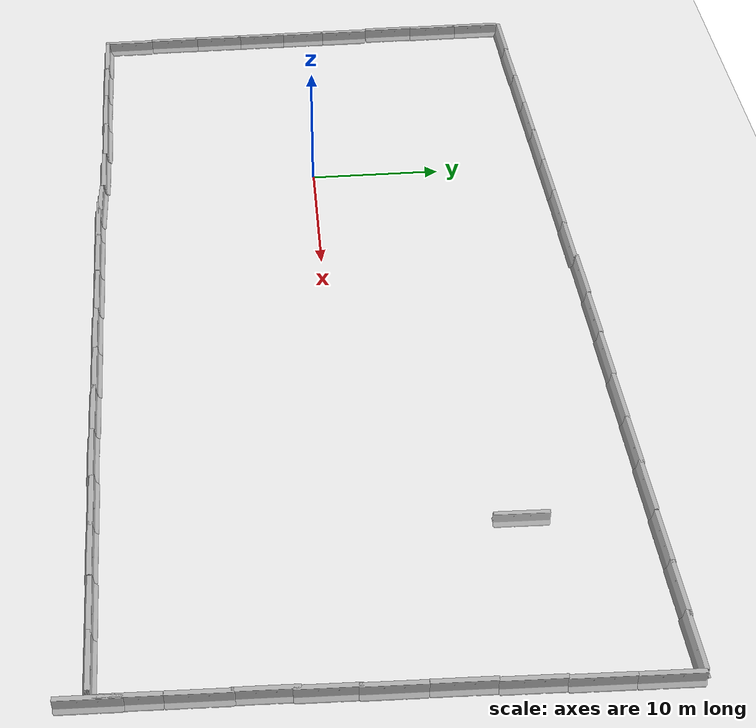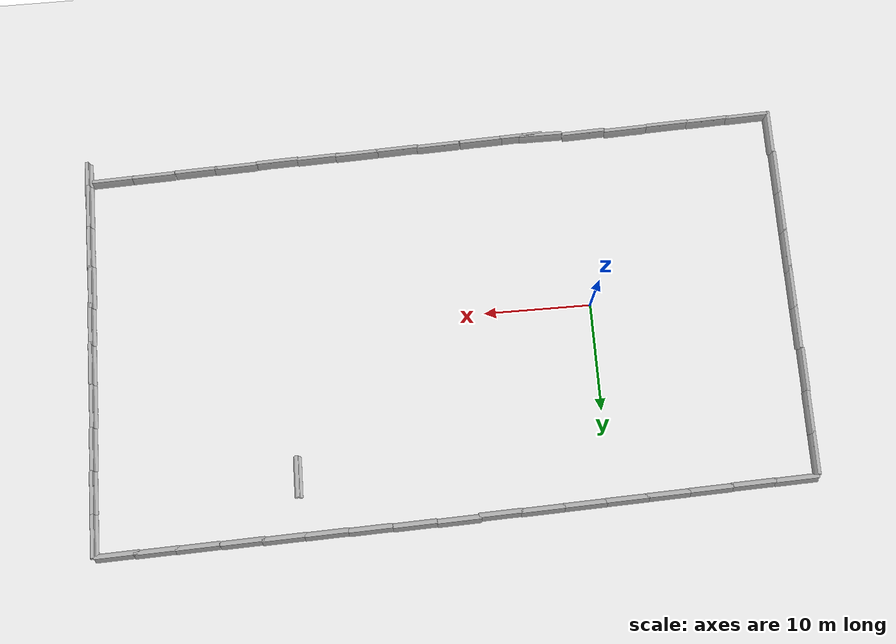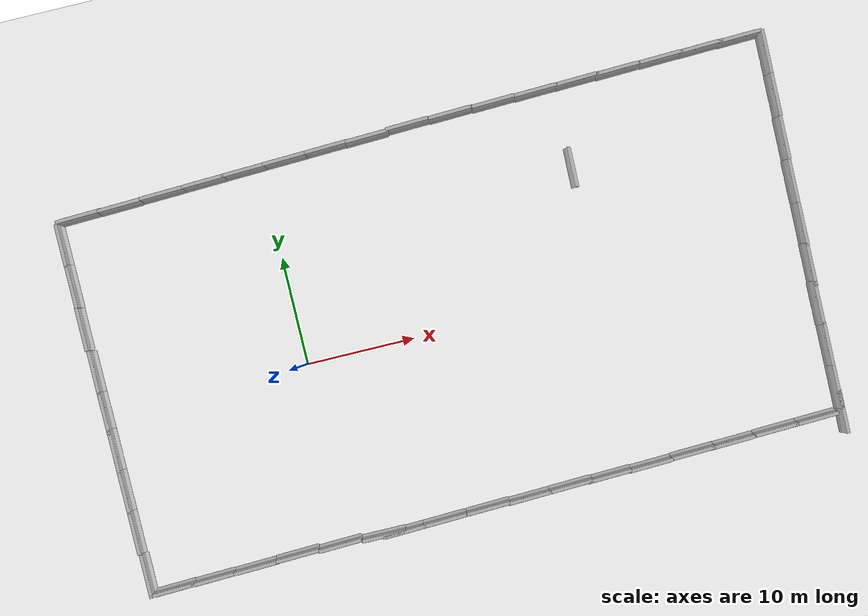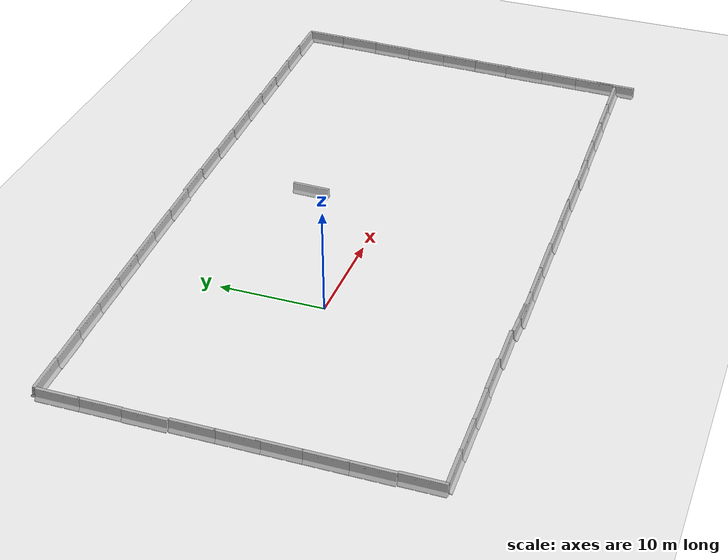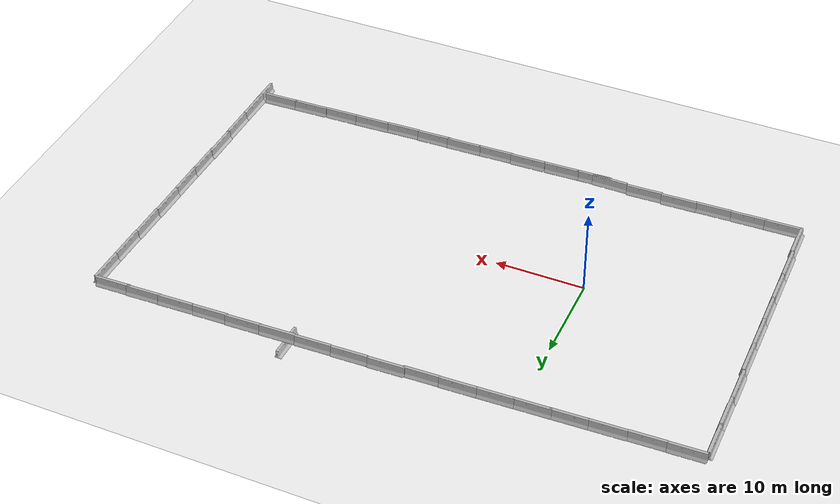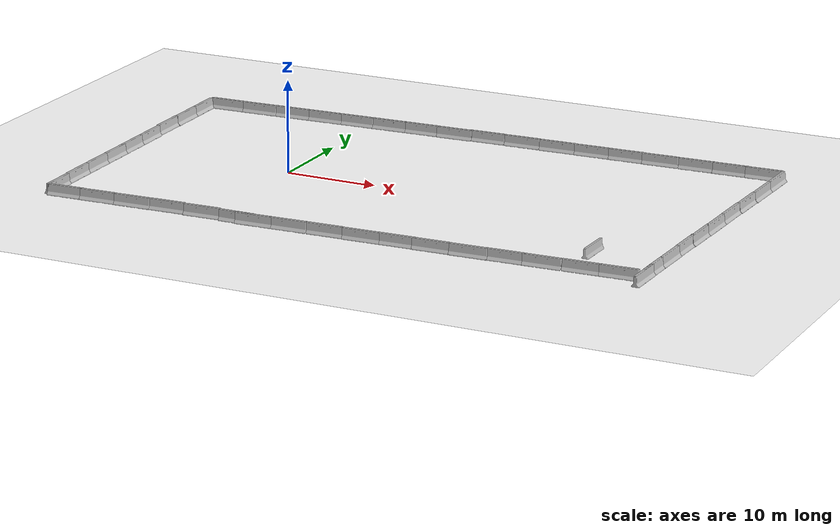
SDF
<sdf version="1.6">
 <world name="default">
  <light name="sun" type="directional">
   <pose>0 0 10 0 -0 0</pose>
   <diffuse>0.8 0.8 0.8 1</diffuse>
   <specular>0.2 0.2 0.2 1</specular>
   <attenuation>
    <range>1000</range>
    <constant>0.9</constant>
    <linear>0.01</linear>
    <quadratic>0.001</quadratic>
   </attenuation>
   <direction>-0.5 0.1 -0.9</direction>
  </light>
  <model name="ground_plane">
   <static>1</static>
   <link name="link">
    <collision name="collision">
     <geometry><plane><normal>0 0 1</normal><size>100 100</size></plane></geometry>
     <surface><friction><ode><mu>100</mu><mu2>50</mu2></ode></friction></surface>
    </collision>
    <visual name="visual">
     <cast_shadows>0</cast_shadows>
     <geometry><plane><normal>0 0 1</normal><size>100 100</size></plane></geometry>
     <material>
      <script><uri>file://media/materials/scripts/gazebo.material</uri><name>Gazebo/Grey</name></script>
     </material>
    </visual>
   </link>
  </model>
  <physics name="default_physics" default="0" type="ode">
   <max_step_size>0.01</max_step_size>
   <real_time_factor>1</real_time_factor>
   <real_time_update_rate>100</real_time_update_rate>
  </physics>
  <gravity>0 0 -9.8</gravity>
  <magnetic_field>6e-06 2.3e-05 -4.2e-05</magnetic_field>
  <atmosphere type="adiabatic"/>
  <scene><ambient>0.4 0.4 0.4 1</ambient><background>0.7 0.7 0.7 1</background><shadows>1</shadows></scene>
  <spherical_coordinates>
   <surface_model>EARTH_WGS84</surface_model>
   <latitude_deg>0</latitude_deg>
   <longitude_deg>0</longitude_deg>
   <elevation>0</elevation>
   <heading_deg>0</heading_deg>
  </spherical_coordinates>
  <model name="jersey_barrier">
   <static>1</static>
   <link name="link">
    <visual name="visual">
     <geometry>
      <mesh><uri>model://jersey_barrier/meshes/jersey_barrier.dae</uri><scale>1 1 1</scale></mesh>
     </geometry>
    </visual>
    <collision name="upright">
     <pose>0 0 0.5715 0 -0 0</pose>
     <geometry><box><size>4.06542 0.3063 1.143</size></box></geometry>
    </collision>
    <collision name="base">
     <pose>0 0 0.032258 0 -0 0</pose>
     <geometry><box><size>4.06542 0.8107 0.064516</size></box></geometry>
    </collision>
    <collision name="base2">
     <pose>0 0 0.1 0 -0 0</pose>
     <geometry><box><size>4.06542 0.65 0.1</size></box></geometry>
    </collision>
    <collision name="base3">
     <pose>0 0 0.2 0 -0 0</pose>
     <geometry><box><size>4.06542 0.5 0.1</size></box></geometry>
    </collision>
    <collision name="left-angle">
     <pose>0 -0.224 0.2401 0.9 -0 0</pose>
     <geometry><box><size>4.06542 0.5 0.064516</size></box></geometry>
    </collision>
    <collision name="right-angle">
     <pose>0 0.224 0.2401 -0.9 0 0</pose>
     <geometry><box><size>4.06542 0.5 0.064516</size></box></geometry>
    </collision>
   </link>
   <pose>-0.913416 -16.6952 0 0 -0 0.033275</pose>
  </model>
  <model name="jersey_barrier_clone">
   <static>1</static>
   <link name="link">
    <visual name="visual">
     <geometry>
      <mesh><uri>model://jersey_barrier/meshes/jersey_barrier.dae</uri><scale>1 1 1</scale></mesh>
     </geometry>
    </visual>
    <collision name="upright">
     <pose>0 0 0.5715 0 -0 0</pose>
     <geometry><box><size>4.06542 0.3063 1.143</size></box></geometry>
    </collision>
    <collision name="base">
     <pose>0 0 0.032258 0 -0 0</pose>
     <geometry><box><size>4.06542 0.8107 0.064516</size></box></geometry>
    </collision>
    <collision name="base2">
     <pose>0 0 0.1 0 -0 0</pose>
     <geometry><box><size>4.06542 0.65 0.1</size></box></geometry>
    </collision>
    <collision name="base3">
     <pose>0 0 0.2 0 -0 0</pose>
     <geometry><box><size>4.06542 0.5 0.1</size></box></geometry>
    </collision>
    <collision name="left-angle">
     <pose>0 -0.224 0.2401 0.9 -0 0</pose>
     <geometry><box><size>4.06542 0.5 0.064516</size></box></geometry>
    </collision>
    <collision name="right-angle">
     <pose>0 0.224 0.2401 -0.9 0 0</pose>
     <geometry><box><size>4.06542 0.5 0.064516</size></box></geometry>
    </collision>
   </link>
   <pose>5.06368 -16.8524 0 0 -0 0.033275</pose>
  </model>
  <model name="jersey_barrier_clone_clone">
   <static>1</static>
   <link name="link">
    <visual name="visual">
     <geometry>
      <mesh><uri>model://jersey_barrier/meshes/jersey_barrier.dae</uri><scale>1 1 1</scale></mesh>
     </geometry>
    </visual>
    <collision name="upright">
     <pose>0 0 0.5715 0 -0 0</pose>
     <geometry><box><size>4.06542 0.3063 1.143</size></box></geometry>
    </collision>
    <collision name="base">
     <pose>0 0 0.032258 0 -0 0</pose>
     <geometry><box><size>4.06542 0.8107 0.064516</size></box></geometry>
    </collision>
    <collision name="base2">
     <pose>0 0 0.1 0 -0 0</pose>
     <geometry><box><size>4.06542 0.65 0.1</size></box></geometry>
    </collision>
    <collision name="base3">
     <pose>0 0 0.2 0 -0 0</pose>
     <geometry><box><size>4.06542 0.5 0.1</size></box></geometry>
    </collision>
    <collision name="left-angle">
     <pose>0 -0.224 0.2401 0.9 -0 0</pose>
     <geometry><box><size>4.06542 0.5 0.064516</size></box></geometry>
    </collision>
    <collision name="right-angle">
     <pose>0 0.224 0.2401 -0.9 0 0</pose>
     <geometry><box><size>4.06542 0.5 0.064516</size></box></geometry>
    </collision>
   </link>
   <pose>-4.93978 -16.7019 0 0 -0 0.033275</pose>
  </model>
  <model name="jersey_barrier_clone_clone_0">
   <static>1</static>
   <link name="link">
    <visual name="visual">
     <geometry>
      <mesh><uri>model://jersey_barrier/meshes/jersey_barrier.dae</uri><scale>1 1 1</scale></mesh>
     </geometry>
    </visual>
    <collision name="upright">
     <pose>0 0 0.5715 0 -0 0</pose>
     <geometry><box><size>4.06542 0.3063 1.143</size></box></geometry>
    </collision>
    <collision name="base">
     <pose>0 0 0.032258 0 -0 0</pose>
     <geometry><box><size>4.06542 0.8107 0.064516</size></box></geometry>
    </collision>
    <collision name="base2">
     <pose>0 0 0.1 0 -0 0</pose>
     <geometry><box><size>4.06542 0.65 0.1</size></box></geometry>
    </collision>
    <collision name="base3">
     <pose>0 0 0.2 0 -0 0</pose>
     <geometry><box><size>4.06542 0.5 0.1</size></box></geometry>
    </collision>
    <collision name="left-angle">
     <pose>0 -0.224 0.2401 0.9 -0 0</pose>
     <geometry><box><size>4.06542 0.5 0.064516</size></box></geometry>
    </collision>
    <collision name="right-angle">
     <pose>0 0.224 0.2401 -0.9 0 0</pose>
     <geometry><box><size>4.06542 0.5 0.064516</size></box></geometry>
    </collision>
   </link>
   <pose>8.87687 -16.7227 0 0 -0 0.033275</pose>
  </model>
  <model name="jersey_barrier_clone_clone_1">
   <static>1</static>
   <link name="link">
    <visual name="visual">
     <geometry>
      <mesh><uri>model://jersey_barrier/meshes/jersey_barrier.dae</uri><scale>1 1 1</scale></mesh>
     </geometry>
    </visual>
    <collision name="upright">
     <pose>0 0 0.5715 0 -0 0</pose>
     <geometry><box><size>4.06542 0.3063 1.143</size></box></geometry>
    </collision>
    <collision name="base">
     <pose>0 0 0.032258 0 -0 0</pose>
     <geometry><box><size>4.06542 0.8107 0.064516</size></box></geometry>
    </collision>
    <collision name="base2">
     <pose>0 0 0.1 0 -0 0</pose>
     <geometry><box><size>4.06542 0.65 0.1</size></box></geometry>
    </collision>
    <collision name="base3">
     <pose>0 0 0.2 0 -0 0</pose>
     <geometry><box><size>4.06542 0.5 0.1</size></box></geometry>
    </collision>
    <collision name="left-angle">
     <pose>0 -0.224 0.2401 0.9 -0 0</pose>
     <geometry><box><size>4.06542 0.5 0.064516</size></box></geometry>
    </collision>
    <collision name="right-angle">
     <pose>0 0.224 0.2401 -0.9 0 0</pose>
     <geometry><box><size>4.06542 0.5 0.064516</size></box></geometry>
    </collision>
   </link>
   <pose>12.9707 -16.5908 0 0 -0 0.033275</pose>
  </model>
  <model name="jersey_barrier_clone_clone_2">
   <static>1</static>
   <link name="link">
    <visual name="visual">
     <geometry>
      <mesh><uri>model://jersey_barrier/meshes/jersey_barrier.dae</uri><scale>1 1 1</scale></mesh>
     </geometry>
    </visual>
    <collision name="upright">
     <pose>0 0 0.5715 0 -0 0</pose>
     <geometry><box><size>4.06542 0.3063 1.143</size></box></geometry>
    </collision>
    <collision name="base">
     <pose>0 0 0.032258 0 -0 0</pose>
     <geometry><box><size>4.06542 0.8107 0.064516</size></box></geometry>
    </collision>
    <collision name="base2">
     <pose>0 0 0.1 0 -0 0</pose>
     <geometry><box><size>4.06542 0.65 0.1</size></box></geometry>
    </collision>
    <collision name="base3">
     <pose>0 0 0.2 0 -0 0</pose>
     <geometry><box><size>4.06542 0.5 0.1</size></box></geometry>
    </collision>
    <collision name="left-angle">
     <pose>0 -0.224 0.2401 0.9 -0 0</pose>
     <geometry><box><size>4.06542 0.5 0.064516</size></box></geometry>
    </collision>
    <collision name="right-angle">
     <pose>0 0.224 0.2401 -0.9 0 0</pose>
     <geometry><box><size>4.06542 0.5 0.064516</size></box></geometry>
    </collision>
   </link>
   <pose>16.8898 -16.5319 0 0 -0 0.033275</pose>
  </model>
  <model name="jersey_barrier_clone_clone_3">
   <static>1</static>
   <link name="link">
    <visual name="visual">
     <geometry>
      <mesh><uri>model://jersey_barrier/meshes/jersey_barrier.dae</uri><scale>1 1 1</scale></mesh>
     </geometry>
    </visual>
    <collision name="upright">
     <pose>0 0 0.5715 0 -0 0</pose>
     <geometry><box><size>4.06542 0.3063 1.143</size></box></geometry>
    </collision>
    <collision name="base">
     <pose>0 0 0.032258 0 -0 0</pose>
     <geometry><box><size>4.06542 0.8107 0.064516</size></box></geometry>
    </collision>
    <collision name="base2">
     <pose>0 0 0.1 0 -0 0</pose>
     <geometry><box><size>4.06542 0.65 0.1</size></box></geometry>
    </collision>
    <collision name="base3">
     <pose>0 0 0.2 0 -0 0</pose>
     <geometry><box><size>4.06542 0.5 0.1</size></box></geometry>
    </collision>
    <collision name="left-angle">
     <pose>0 -0.224 0.2401 0.9 -0 0</pose>
     <geometry><box><size>4.06542 0.5 0.064516</size></box></geometry>
    </collision>
    <collision name="right-angle">
     <pose>0 0.224 0.2401 -0.9 0 0</pose>
     <geometry><box><size>4.06542 0.5 0.064516</size></box></geometry>
    </collision>
   </link>
   <pose>20.7541 -16.3983 0 0 -0 0.033275</pose>
  </model>
  <model name="jersey_barrier_clone_clone_clone">
   <static>1</static>
   <link name="link">
    <visual name="visual">
     <geometry>
      <mesh><uri>model://jersey_barrier/meshes/jersey_barrier.dae</uri><scale>1 1 1</scale></mesh>
     </geometry>
    </visual>
    <collision name="upright">
     <pose>0 0 0.5715 0 -0 0</pose>
     <geometry><box><size>4.06542 0.3063 1.143</size></box></geometry>
    </collision>
    <collision name="base">
     <pose>0 0 0.032258 0 -0 0</pose>
     <geometry><box><size>4.06542 0.8107 0.064516</size></box></geometry>
    </collision>
    <collision name="base2">
     <pose>0 0 0.1 0 -0 0</pose>
     <geometry><box><size>4.06542 0.65 0.1</size></box></geometry>
    </collision>
    <collision name="base3">
     <pose>0 0 0.2 0 -0 0</pose>
     <geometry><box><size>4.06542 0.5 0.1</size></box></geometry>
    </collision>
    <collision name="left-angle">
     <pose>0 -0.224 0.2401 0.9 -0 0</pose>
     <geometry><box><size>4.06542 0.5 0.064516</size></box></geometry>
    </collision>
    <collision name="right-angle">
     <pose>0 0.224 0.2401 -0.9 0 0</pose>
     <geometry><box><size>4.06542 0.5 0.064516</size></box></geometry>
    </collision>
   </link>
   <pose>24.4141 -16.3295 0 0 -0 0.033275</pose>
  </model>
  <model name="jersey_barrier_clone_clone_clone_0">
   <static>1</static>
   <link name="link">
    <visual name="visual">
     <geometry>
      <mesh><uri>model://jersey_barrier/meshes/jersey_barrier.dae</uri><scale>1 1 1</scale></mesh>
     </geometry>
    </visual>
    <collision name="upright">
     <pose>0 0 0.5715 0 -0 0</pose>
     <geometry><box><size>4.06542 0.3063 1.143</size></box></geometry>
    </collision>
    <collision name="base">
     <pose>0 0 0.032258 0 -0 0</pose>
     <geometry><box><size>4.06542 0.8107 0.064516</size></box></geometry>
    </collision>
    <collision name="base2">
     <pose>0 0 0.1 0 -0 0</pose>
     <geometry><box><size>4.06542 0.65 0.1</size></box></geometry>
    </collision>
    <collision name="base3">
     <pose>0 0 0.2 0 -0 0</pose>
     <geometry><box><size>4.06542 0.5 0.1</size></box></geometry>
    </collision>
    <collision name="left-angle">
     <pose>0 -0.224 0.2401 0.9 -0 0</pose>
     <geometry><box><size>4.06542 0.5 0.064516</size></box></geometry>
    </collision>
    <collision name="right-angle">
     <pose>0 0.224 0.2401 -0.9 0 0</pose>
     <geometry><box><size>4.06542 0.5 0.064516</size></box></geometry>
    </collision>
   </link>
   <pose>-8.88852 -16.868 0 0 -0 0.033275</pose>
  </model>
  <model name="jersey_barrier_clone_clone_clone_2">
   <static>1</static>
   <link name="link">
    <visual name="visual">
     <geometry>
      <mesh><uri>model://jersey_barrier/meshes/jersey_barrier.dae</uri><scale>1 1 1</scale></mesh>
     </geometry>
    </visual>
    <collision name="upright">
     <pose>0 0 0.5715 0 -0 0</pose>
     <geometry><box><size>4.06542 0.3063 1.143</size></box></geometry>
    </collision>
    <collision name="base">
     <pose>0 0 0.032258 0 -0 0</pose>
     <geometry><box><size>4.06542 0.8107 0.064516</size></box></geometry>
    </collision>
    <collision name="base2">
     <pose>0 0 0.1 0 -0 0</pose>
     <geometry><box><size>4.06542 0.65 0.1</size></box></geometry>
    </collision>
    <collision name="base3">
     <pose>0 0 0.2 0 -0 0</pose>
     <geometry><box><size>4.06542 0.5 0.1</size></box></geometry>
    </collision>
    <collision name="left-angle">
     <pose>0 -0.224 0.2401 0.9 -0 0</pose>
     <geometry><box><size>4.06542 0.5 0.064516</size></box></geometry>
    </collision>
    <collision name="right-angle">
     <pose>0 0.224 0.2401 -0.9 0 0</pose>
     <geometry><box><size>4.06542 0.5 0.064516</size></box></geometry>
    </collision>
   </link>
   <pose>-12.8673 -16.9656 0 0 -0 0.033275</pose>
  </model>
  <model name="jersey_barrier_clone_clone_clone_clone">
   <static>1</static>
   <link name="link">
    <visual name="visual">
     <geometry>
      <mesh><uri>model://jersey_barrier/meshes/jersey_barrier.dae</uri><scale>1 1 1</scale></mesh>
     </geometry>
    </visual>
    <collision name="upright">
     <pose>0 0 0.5715 0 -0 0</pose>
     <geometry><box><size>4.06542 0.3063 1.143</size></box></geometry>
    </collision>
    <collision name="base">
     <pose>0 0 0.032258 0 -0 0</pose>
     <geometry><box><size>4.06542 0.8107 0.064516</size></box></geometry>
    </collision>
    <collision name="base2">
     <pose>0 0 0.1 0 -0 0</pose>
     <geometry><box><size>4.06542 0.65 0.1</size></box></geometry>
    </collision>
    <collision name="base3">
     <pose>0 0 0.2 0 -0 0</pose>
     <geometry><box><size>4.06542 0.5 0.1</size></box></geometry>
    </collision>
    <collision name="left-angle">
     <pose>0 -0.224 0.2401 0.9 -0 0</pose>
     <geometry><box><size>4.06542 0.5 0.064516</size></box></geometry>
    </collision>
    <collision name="right-angle">
     <pose>0 0.224 0.2401 -0.9 0 0</pose>
     <geometry><box><size>4.06542 0.5 0.064516</size></box></geometry>
    </collision>
   </link>
   <pose>28.3606 -16.2557 0 0 -0 0.033275</pose>
  </model>
  <model name="jersey_barrier_clone_clone_clone_3_clone_clone_2">
   <static>1</static>
   <link name="link">
    <visual name="visual">
     <geometry>
      <mesh><uri>model://jersey_barrier/meshes/jersey_barrier.dae</uri><scale>1 1 1</scale></mesh>
     </geometry>
    </visual>
    <collision name="upright">
     <pose>0 0 0.5715 0 -0 0</pose>
     <geometry><box><size>4.06542 0.3063 1.143</size></box></geometry>
    </collision>
    <collision name="base">
     <pose>0 0 0.032258 0 -0 0</pose>
     <geometry><box><size>4.06542 0.8107 0.064516</size></box></geometry>
    </collision>
    <collision name="base2">
     <pose>0 0 0.1 0 -0 0</pose>
     <geometry><box><size>4.06542 0.65 0.1</size></box></geometry>
    </collision>
    <collision name="base3">
     <pose>0 0 0.2 0 -0 0</pose>
     <geometry><box><size>4.06542 0.5 0.1</size></box></geometry>
    </collision>
    <collision name="left-angle">
     <pose>0 -0.224 0.2401 0.9 -0 0</pose>
     <geometry><box><size>4.06542 0.5 0.064516</size></box></geometry>
    </collision>
    <collision name="right-angle">
     <pose>0 0.224 0.2401 -0.9 0 0</pose>
     <geometry><box><size>4.06542 0.5 0.064516</size></box></geometry>
    </collision>
   </link>
   <pose>29.0417 12.8143 -8.43284 0 0 -1.5926</pose>
  </model>
  <model name="jersey_barrier_clone_clone_clone_clone_0">
   <static>1</static>
   <link name="link">
    <visual name="visual">
     <geometry>
      <mesh><uri>model://jersey_barrier/meshes/jersey_barrier.dae</uri><scale>1 1 1</scale></mesh>
     </geometry>
    </visual>
    <collision name="upright">
     <pose>0 0 0.5715 0 -0 0</pose>
     <geometry><box><size>4.06542 0.3063 1.143</size></box></geometry>
    </collision>
    <collision name="base">
     <pose>0 0 0.032258 0 -0 0</pose>
     <geometry><box><size>4.06542 0.8107 0.064516</size></box></geometry>
    </collision>
    <collision name="base2">
     <pose>0 0 0.1 0 -0 0</pose>
     <geometry><box><size>4.06542 0.65 0.1</size></box></geometry>
    </collision>
    <collision name="base3">
     <pose>0 0 0.2 0 -0 0</pose>
     <geometry><box><size>4.06542 0.5 0.1</size></box></geometry>
    </collision>
    <collision name="left-angle">
     <pose>0 -0.224 0.2401 0.9 -0 0</pose>
     <geometry><box><size>4.06542 0.5 0.064516</size></box></geometry>
    </collision>
    <collision name="right-angle">
     <pose>0 0.224 0.2401 -0.9 0 0</pose>
     <geometry><box><size>4.06542 0.5 0.064516</size></box></geometry>
    </collision>
   </link>
   <pose>26.0844 19.3245 0 0 -0 0.033275</pose>
  </model>
  <model name="jersey_barrier_clone_clone_clone_clone_0_clone">
   <static>1</static>
   <link name="link">
    <visual name="visual">
     <geometry>
      <mesh><uri>model://jersey_barrier/meshes/jersey_barrier.dae</uri><scale>1 1 1</scale></mesh>
     </geometry>
    </visual>
    <collision name="upright">
     <pose>0 0 0.5715 0 -0 0</pose>
     <geometry><box><size>4.06542 0.3063 1.143</size></box></geometry>
    </collision>
    <collision name="base">
     <pose>0 0 0.032258 0 -0 0</pose>
     <geometry><box><size>4.06542 0.8107 0.064516</size></box></geometry>
    </collision>
    <collision name="base2">
     <pose>0 0 0.1 0 -0 0</pose>
     <geometry><box><size>4.06542 0.65 0.1</size></box></geometry>
    </collision>
    <collision name="base3">
     <pose>0 0 0.2 0 -0 0</pose>
     <geometry><box><size>4.06542 0.5 0.1</size></box></geometry>
    </collision>
    <collision name="left-angle">
     <pose>0 -0.224 0.2401 0.9 -0 0</pose>
     <geometry><box><size>4.06542 0.5 0.064516</size></box></geometry>
    </collision>
    <collision name="right-angle">
     <pose>0 0.224 0.2401 -0.9 0 0</pose>
     <geometry><box><size>4.06542 0.5 0.064516</size></box></geometry>
    </collision>
   </link>
   <pose>22.068 19.2501 0 0 -0 0.033275</pose>
  </model>
  <model name="jersey_barrier_clone_clone_clone_clone_0_clone_0">
   <static>1</static>
   <link name="link">
    <visual name="visual">
     <geometry>
      <mesh><uri>model://jersey_barrier/meshes/jersey_barrier.dae</uri><scale>1 1 1</scale></mesh>
     </geometry>
    </visual>
    <collision name="upright">
     <pose>0 0 0.5715 0 -0 0</pose>
     <geometry><box><size>4.06542 0.3063 1.143</size></box></geometry>
    </collision>
    <collision name="base">
     <pose>0 0 0.032258 0 -0 0</pose>
     <geometry><box><size>4.06542 0.8107 0.064516</size></box></geometry>
    </collision>
    <collision name="base2">
     <pose>0 0 0.1 0 -0 0</pose>
     <geometry><box><size>4.06542 0.65 0.1</size></box></geometry>
    </collision>
    <collision name="base3">
     <pose>0 0 0.2 0 -0 0</pose>
     <geometry><box><size>4.06542 0.5 0.1</size></box></geometry>
    </collision>
    <collision name="left-angle">
     <pose>0 -0.224 0.2401 0.9 -0 0</pose>
     <geometry><box><size>4.06542 0.5 0.064516</size></box></geometry>
    </collision>
    <collision name="right-angle">
     <pose>0 0.224 0.2401 -0.9 0 0</pose>
     <geometry><box><size>4.06542 0.5 0.064516</size></box></geometry>
    </collision>
   </link>
   <pose>18.0097 19.1749 0 0 -0 0.033275</pose>
  </model>
  <model name="jersey_barrier_clone_clone_clone_clone_0_clone_0_clone">
   <static>1</static>
   <link name="link">
    <visual name="visual">
     <geometry>
      <mesh><uri>model://jersey_barrier/meshes/jersey_barrier.dae</uri><scale>1 1 1</scale></mesh>
     </geometry>
    </visual>
    <collision name="upright">
     <pose>0 0 0.5715 0 -0 0</pose>
     <geometry><box><size>4.06542 0.3063 1.143</size></box></geometry>
    </collision>
    <collision name="base">
     <pose>0 0 0.032258 0 -0 0</pose>
     <geometry><box><size>4.06542 0.8107 0.064516</size></box></geometry>
    </collision>
    <collision name="base2">
     <pose>0 0 0.1 0 -0 0</pose>
     <geometry><box><size>4.06542 0.65 0.1</size></box></geometry>
    </collision>
    <collision name="base3">
     <pose>0 0 0.2 0 -0 0</pose>
     <geometry><box><size>4.06542 0.5 0.1</size></box></geometry>
    </collision>
    <collision name="left-angle">
     <pose>0 -0.224 0.2401 0.9 -0 0</pose>
     <geometry><box><size>4.06542 0.5 0.064516</size></box></geometry>
    </collision>
    <collision name="right-angle">
     <pose>0 0.224 0.2401 -0.9 0 0</pose>
     <geometry><box><size>4.06542 0.5 0.064516</size></box></geometry>
    </collision>
   </link>
   <pose>13.949 19.1026 0 0 -0 0.033275</pose>
  </model>
  <model name="jersey_barrier_clone_clone_clone_clone_0_clone_0_clone_clone">
   <static>1</static>
   <link name="link">
    <visual name="visual">
     <geometry>
      <mesh><uri>model://jersey_barrier/meshes/jersey_barrier.dae</uri><scale>1 1 1</scale></mesh>
     </geometry>
    </visual>
    <collision name="upright">
     <pose>0 0 0.5715 0 -0 0</pose>
     <geometry><box><size>4.06542 0.3063 1.143</size></box></geometry>
    </collision>
    <collision name="base">
     <pose>0 0 0.032258 0 -0 0</pose>
     <geometry><box><size>4.06542 0.8107 0.064516</size></box></geometry>
    </collision>
    <collision name="base2">
     <pose>0 0 0.1 0 -0 0</pose>
     <geometry><box><size>4.06542 0.65 0.1</size></box></geometry>
    </collision>
    <collision name="base3">
     <pose>0 0 0.2 0 -0 0</pose>
     <geometry><box><size>4.06542 0.5 0.1</size></box></geometry>
    </collision>
    <collision name="left-angle">
     <pose>0 -0.224 0.2401 0.9 -0 0</pose>
     <geometry><box><size>4.06542 0.5 0.064516</size></box></geometry>
    </collision>
    <collision name="right-angle">
     <pose>0 0.224 0.2401 -0.9 0 0</pose>
     <geometry><box><size>4.06542 0.5 0.064516</size></box></geometry>
    </collision>
   </link>
   <pose>10.1358 18.8674 0 0 -0 0.033275</pose>
  </model>
  <model name="jersey_barrier_clone_clone_clone_clone_0_clone_0_clone_clone_0">
   <static>1</static>
   <link name="link">
    <visual name="visual">
     <geometry>
      <mesh><uri>model://jersey_barrier/meshes/jersey_barrier.dae</uri><scale>1 1 1</scale></mesh>
     </geometry>
    </visual>
    <collision name="upright">
     <pose>0 0 0.5715 0 -0 0</pose>
     <geometry><box><size>4.06542 0.3063 1.143</size></box></geometry>
    </collision>
    <collision name="base">
     <pose>0 0 0.032258 0 -0 0</pose>
     <geometry><box><size>4.06542 0.8107 0.064516</size></box></geometry>
    </collision>
    <collision name="base2">
     <pose>0 0 0.1 0 -0 0</pose>
     <geometry><box><size>4.06542 0.65 0.1</size></box></geometry>
    </collision>
    <collision name="base3">
     <pose>0 0 0.2 0 -0 0</pose>
     <geometry><box><size>4.06542 0.5 0.1</size></box></geometry>
    </collision>
    <collision name="left-angle">
     <pose>0 -0.224 0.2401 0.9 -0 0</pose>
     <geometry><box><size>4.06542 0.5 0.064516</size></box></geometry>
    </collision>
    <collision name="right-angle">
     <pose>0 0.224 0.2401 -0.9 0 0</pose>
     <geometry><box><size>4.06542 0.5 0.064516</size></box></geometry>
    </collision>
   </link>
   <pose>6.27406 18.7774 0 0 -0 0.033275</pose>
  </model>
  <model name="jersey_barrier_clone_clone_clone_clone_0_clone_0_clone_clone_1">
   <static>1</static>
   <link name="link">
    <visual name="visual">
     <geometry>
      <mesh><uri>model://jersey_barrier/meshes/jersey_barrier.dae</uri><scale>1 1 1</scale></mesh>
     </geometry>
    </visual>
    <collision name="upright">
     <pose>0 0 0.5715 0 -0 0</pose>
     <geometry><box><size>4.06542 0.3063 1.143</size></box></geometry>
    </collision>
    <collision name="base">
     <pose>0 0 0.032258 0 -0 0</pose>
     <geometry><box><size>4.06542 0.8107 0.064516</size></box></geometry>
    </collision>
    <collision name="base2">
     <pose>0 0 0.1 0 -0 0</pose>
     <geometry><box><size>4.06542 0.65 0.1</size></box></geometry>
    </collision>
    <collision name="base3">
     <pose>0 0 0.2 0 -0 0</pose>
     <geometry><box><size>4.06542 0.5 0.1</size></box></geometry>
    </collision>
    <collision name="left-angle">
     <pose>0 -0.224 0.2401 0.9 -0 0</pose>
     <geometry><box><size>4.06542 0.5 0.064516</size></box></geometry>
    </collision>
    <collision name="right-angle">
     <pose>0 0.224 0.2401 -0.9 0 0</pose>
     <geometry><box><size>4.06542 0.5 0.064516</size></box></geometry>
    </collision>
   </link>
   <pose>2.36253 18.639 0 0 -0 0.033275</pose>
  </model>
  <model name="jersey_barrier_clone_clone_clone_clone_0_clone_0_clone_clone_2">
   <static>1</static>
   <link name="link">
    <visual name="visual">
     <geometry>
      <mesh><uri>model://jersey_barrier/meshes/jersey_barrier.dae</uri><scale>1 1 1</scale></mesh>
     </geometry>
    </visual>
    <collision name="upright">
     <pose>0 0 0.5715 0 -0 0</pose>
     <geometry><box><size>4.06542 0.3063 1.143</size></box></geometry>
    </collision>
    <collision name="base">
     <pose>0 0 0.032258 0 -0 0</pose>
     <geometry><box><size>4.06542 0.8107 0.064516</size></box></geometry>
    </collision>
    <collision name="base2">
     <pose>0 0 0.1 0 -0 0</pose>
     <geometry><box><size>4.06542 0.65 0.1</size></box></geometry>
    </collision>
    <collision name="base3">
     <pose>0 0 0.2 0 -0 0</pose>
     <geometry><box><size>4.06542 0.5 0.1</size></box></geometry>
    </collision>
    <collision name="left-angle">
     <pose>0 -0.224 0.2401 0.9 -0 0</pose>
     <geometry><box><size>4.06542 0.5 0.064516</size></box></geometry>
    </collision>
    <collision name="right-angle">
     <pose>0 0.224 0.2401 -0.9 0 0</pose>
     <geometry><box><size>4.06542 0.5 0.064516</size></box></geometry>
    </collision>
   </link>
   <pose>-1.50152 18.5003 0 0 -0 0.033275</pose>
  </model>
  <model name="jersey_barrier_clone_clone_clone_clone_0_clone_0_clone_clone_3">
   <static>1</static>
   <link name="link">
    <visual name="visual">
     <geometry>
      <mesh><uri>model://jersey_barrier/meshes/jersey_barrier.dae</uri><scale>1 1 1</scale></mesh>
     </geometry>
    </visual>
    <collision name="upright">
     <pose>0 0 0.5715 0 -0 0</pose>
     <geometry><box><size>4.06542 0.3063 1.143</size></box></geometry>
    </collision>
    <collision name="base">
     <pose>0 0 0.032258 0 -0 0</pose>
     <geometry><box><size>4.06542 0.8107 0.064516</size></box></geometry>
    </collision>
    <collision name="base2">
     <pose>0 0 0.1 0 -0 0</pose>
     <geometry><box><size>4.06542 0.65 0.1</size></box></geometry>
    </collision>
    <collision name="base3">
     <pose>0 0 0.2 0 -0 0</pose>
     <geometry><box><size>4.06542 0.5 0.1</size></box></geometry>
    </collision>
    <collision name="left-angle">
     <pose>0 -0.224 0.2401 0.9 -0 0</pose>
     <geometry><box><size>4.06542 0.5 0.064516</size></box></geometry>
    </collision>
    <collision name="right-angle">
     <pose>0 0.224 0.2401 -0.9 0 0</pose>
     <geometry><box><size>4.06542 0.5 0.064516</size></box></geometry>
    </collision>
   </link>
   <pose>-5.27021 18.3618 0 0 -0 0.033275</pose>
  </model>
  <model name="jersey_barrier_clone_clone_clone_clone_0_clone_0_clone_clone_4">
   <static>1</static>
   <link name="link">
    <visual name="visual">
     <geometry>
      <mesh><uri>model://jersey_barrier/meshes/jersey_barrier.dae</uri><scale>1 1 1</scale></mesh>
     </geometry>
    </visual>
    <collision name="upright">
     <pose>0 0 0.5715 0 -0 0</pose>
     <geometry><box><size>4.06542 0.3063 1.143</size></box></geometry>
    </collision>
    <collision name="base">
     <pose>0 0 0.032258 0 -0 0</pose>
     <geometry><box><size>4.06542 0.8107 0.064516</size></box></geometry>
    </collision>
    <collision name="base2">
     <pose>0 0 0.1 0 -0 0</pose>
     <geometry><box><size>4.06542 0.65 0.1</size></box></geometry>
    </collision>
    <collision name="base3">
     <pose>0 0 0.2 0 -0 0</pose>
     <geometry><box><size>4.06542 0.5 0.1</size></box></geometry>
    </collision>
    <collision name="left-angle">
     <pose>0 -0.224 0.2401 0.9 -0 0</pose>
     <geometry><box><size>4.06542 0.5 0.064516</size></box></geometry>
    </collision>
    <collision name="right-angle">
     <pose>0 0.224 0.2401 -0.9 0 0</pose>
     <geometry><box><size>4.06542 0.5 0.064516</size></box></geometry>
    </collision>
   </link>
   <pose>-9.19914 18.219 0 0 -0 0.033275</pose>
  </model>
  <model name="jersey_barrier_clone_clone_clone_clone_0_clone_0_clone_clone_4_clone">
   <static>1</static>
   <link name="link">
    <visual name="visual">
     <geometry>
      <mesh><uri>model://jersey_barrier/meshes/jersey_barrier.dae</uri><scale>1 1 1</scale></mesh>
     </geometry>
    </visual>
    <collision name="upright">
     <pose>0 0 0.5715 0 -0 0</pose>
     <geometry><box><size>4.06542 0.3063 1.143</size></box></geometry>
    </collision>
    <collision name="base">
     <pose>0 0 0.032258 0 -0 0</pose>
     <geometry><box><size>4.06542 0.8107 0.064516</size></box></geometry>
    </collision>
    <collision name="base2">
     <pose>0 0 0.1 0 -0 0</pose>
     <geometry><box><size>4.06542 0.65 0.1</size></box></geometry>
    </collision>
    <collision name="base3">
     <pose>0 0 0.2 0 -0 0</pose>
     <geometry><box><size>4.06542 0.5 0.1</size></box></geometry>
    </collision>
    <collision name="left-angle">
     <pose>0 -0.224 0.2401 0.9 -0 0</pose>
     <geometry><box><size>4.06542 0.5 0.064516</size></box></geometry>
    </collision>
    <collision name="right-angle">
     <pose>0 0.224 0.2401 -0.9 0 0</pose>
     <geometry><box><size>4.06542 0.5 0.064516</size></box></geometry>
    </collision>
   </link>
   <pose>-13.2057 18.0477 0 0 -0 0.033275</pose>
  </model>
  <model name="jersey_barrier_clone_clone_clone_clone_0_clone_0_clone_clone_4_clone_clone">
   <static>1</static>
   <link name="link">
    <visual name="visual">
     <geometry>
      <mesh><uri>model://jersey_barrier/meshes/jersey_barrier.dae</uri><scale>1 1 1</scale></mesh>
     </geometry>
    </visual>
    <collision name="upright">
     <pose>0 0 0.5715 0 -0 0</pose>
     <geometry><box><size>4.06542 0.3063 1.143</size></box></geometry>
    </collision>
    <collision name="base">
     <pose>0 0 0.032258 0 -0 0</pose>
     <geometry><box><size>4.06542 0.8107 0.064516</size></box></geometry>
    </collision>
    <collision name="base2">
     <pose>0 0 0.1 0 -0 0</pose>
     <geometry><box><size>4.06542 0.65 0.1</size></box></geometry>
    </collision>
    <collision name="base3">
     <pose>0 0 0.2 0 -0 0</pose>
     <geometry><box><size>4.06542 0.5 0.1</size></box></geometry>
    </collision>
    <collision name="left-angle">
     <pose>0 -0.224 0.2401 0.9 -0 0</pose>
     <geometry><box><size>4.06542 0.5 0.064516</size></box></geometry>
    </collision>
    <collision name="right-angle">
     <pose>0 0.224 0.2401 -0.9 0 0</pose>
     <geometry><box><size>4.06542 0.5 0.064516</size></box></geometry>
    </collision>
   </link>
   <pose>-17.1438 17.9443 0 0 -0 0.033275</pose>
  </model>
  <model name="jersey_barrier_clone_clone_clone_3_clone_clone_1_clone_0">
   <static>1</static>
   <link name="link">
    <visual name="visual">
     <geometry>
      <mesh><uri>model://jersey_barrier/meshes/jersey_barrier.dae</uri><scale>1 1 1</scale></mesh>
     </geometry>
    </visual>
    <collision name="upright">
     <pose>0 0 0.5715 0 -0 0</pose>
     <geometry><box><size>4.06542 0.3063 1.143</size></box></geometry>
    </collision>
    <collision name="base">
     <pose>0 0 0.032258 0 -0 0</pose>
     <geometry><box><size>4.06542 0.8107 0.064516</size></box></geometry>
    </collision>
    <collision name="base2">
     <pose>0 0 0.1 0 -0 0</pose>
     <geometry><box><size>4.06542 0.65 0.1</size></box></geometry>
    </collision>
    <collision name="base3">
     <pose>0 0 0.2 0 -0 0</pose>
     <geometry><box><size>4.06542 0.5 0.1</size></box></geometry>
    </collision>
    <collision name="left-angle">
     <pose>0 -0.224 0.2401 0.9 -0 0</pose>
     <geometry><box><size>4.06542 0.5 0.064516</size></box></geometry>
    </collision>
    <collision name="right-angle">
     <pose>0 0.224 0.2401 -0.9 0 0</pose>
     <geometry><box><size>4.06542 0.5 0.064516</size></box></geometry>
    </collision>
   </link>
   <pose>-19.1448 15.6922 0 0 0 -1.5622</pose>
  </model>
  <model name="jersey_barrier_clone_clone_clone_3_clone_clone_1_clone_0_clone">
   <static>1</static>
   <link name="link">
    <visual name="visual">
     <geometry>
      <mesh><uri>model://jersey_barrier/meshes/jersey_barrier.dae</uri><scale>1 1 1</scale></mesh>
     </geometry>
    </visual>
    <collision name="upright">
     <pose>0 0 0.5715 0 -0 0</pose>
     <geometry><box><size>4.06542 0.3063 1.143</size></box></geometry>
    </collision>
    <collision name="base">
     <pose>0 0 0.032258 0 -0 0</pose>
     <geometry><box><size>4.06542 0.8107 0.064516</size></box></geometry>
    </collision>
    <collision name="base2">
     <pose>0 0 0.1 0 -0 0</pose>
     <geometry><box><size>4.06542 0.65 0.1</size></box></geometry>
    </collision>
    <collision name="base3">
     <pose>0 0 0.2 0 -0 0</pose>
     <geometry><box><size>4.06542 0.5 0.1</size></box></geometry>
    </collision>
    <collision name="left-angle">
     <pose>0 -0.224 0.2401 0.9 -0 0</pose>
     <geometry><box><size>4.06542 0.5 0.064516</size></box></geometry>
    </collision>
    <collision name="right-angle">
     <pose>0 0.224 0.2401 -0.9 0 0</pose>
     <geometry><box><size>4.06542 0.5 0.064516</size></box></geometry>
    </collision>
   </link>
   <pose>-19.1056 11.8976 0 0 0 -1.5622</pose>
  </model>
  <model name="jersey_barrier_clone_clone_clone_3_clone_clone_1_clone_0_clone_0">
   <static>1</static>
   <link name="link">
    <visual name="visual">
     <geometry>
      <mesh><uri>model://jersey_barrier/meshes/jersey_barrier.dae</uri><scale>1 1 1</scale></mesh>
     </geometry>
    </visual>
    <collision name="upright">
     <pose>0 0 0.5715 0 -0 0</pose>
     <geometry><box><size>4.06542 0.3063 1.143</size></box></geometry>
    </collision>
    <collision name="base">
     <pose>0 0 0.032258 0 -0 0</pose>
     <geometry><box><size>4.06542 0.8107 0.064516</size></box></geometry>
    </collision>
    <collision name="base2">
     <pose>0 0 0.1 0 -0 0</pose>
     <geometry><box><size>4.06542 0.65 0.1</size></box></geometry>
    </collision>
    <collision name="base3">
     <pose>0 0 0.2 0 -0 0</pose>
     <geometry><box><size>4.06542 0.5 0.1</size></box></geometry>
    </collision>
    <collision name="left-angle">
     <pose>0 -0.224 0.2401 0.9 -0 0</pose>
     <geometry><box><size>4.06542 0.5 0.064516</size></box></geometry>
    </collision>
    <collision name="right-angle">
     <pose>0 0.224 0.2401 -0.9 0 0</pose>
     <geometry><box><size>4.06542 0.5 0.064516</size></box></geometry>
    </collision>
   </link>
   <pose>-19.118 7.89262 0 0 0 -1.5622</pose>
  </model>
  <model name="jersey_barrier_clone_clone_clone_3_clone_clone_1_clone_0_clone_1">
   <static>1</static>
   <link name="link">
    <visual name="visual">
     <geometry>
      <mesh><uri>model://jersey_barrier/meshes/jersey_barrier.dae</uri><scale>1 1 1</scale></mesh>
     </geometry>
    </visual>
    <collision name="upright">
     <pose>0 0 0.5715 0 -0 0</pose>
     <geometry><box><size>4.06542 0.3063 1.143</size></box></geometry>
    </collision>
    <collision name="base">
     <pose>0 0 0.032258 0 -0 0</pose>
     <geometry><box><size>4.06542 0.8107 0.064516</size></box></geometry>
    </collision>
    <collision name="base2">
     <pose>0 0 0.1 0 -0 0</pose>
     <geometry><box><size>4.06542 0.65 0.1</size></box></geometry>
    </collision>
    <collision name="base3">
     <pose>0 0 0.2 0 -0 0</pose>
     <geometry><box><size>4.06542 0.5 0.1</size></box></geometry>
    </collision>
    <collision name="left-angle">
     <pose>0 -0.224 0.2401 0.9 -0 0</pose>
     <geometry><box><size>4.06542 0.5 0.064516</size></box></geometry>
    </collision>
    <collision name="right-angle">
     <pose>0 0.224 0.2401 -0.9 0 0</pose>
     <geometry><box><size>4.06542 0.5 0.064516</size></box></geometry>
    </collision>
   </link>
   <pose>-18.9683 3.80804 0 0 0 -1.5622</pose>
  </model>
  <model name="jersey_barrier_clone_clone_clone_3_clone_clone_1_clone_0_clone_2">
   <static>1</static>
   <link name="link">
    <visual name="visual">
     <geometry>
      <mesh><uri>model://jersey_barrier/meshes/jersey_barrier.dae</uri><scale>1 1 1</scale></mesh>
     </geometry>
    </visual>
    <collision name="upright">
     <pose>0 0 0.5715 0 -0 0</pose>
     <geometry><box><size>4.06542 0.3063 1.143</size></box></geometry>
    </collision>
    <collision name="base">
     <pose>0 0 0.032258 0 -0 0</pose>
     <geometry><box><size>4.06542 0.8107 0.064516</size></box></geometry>
    </collision>
    <collision name="base2">
     <pose>0 0 0.1 0 -0 0</pose>
     <geometry><box><size>4.06542 0.65 0.1</size></box></geometry>
    </collision>
    <collision name="base3">
     <pose>0 0 0.2 0 -0 0</pose>
     <geometry><box><size>4.06542 0.5 0.1</size></box></geometry>
    </collision>
    <collision name="left-angle">
     <pose>0 -0.224 0.2401 0.9 -0 0</pose>
     <geometry><box><size>4.06542 0.5 0.064516</size></box></geometry>
    </collision>
    <collision name="right-angle">
     <pose>0 0.224 0.2401 -0.9 0 0</pose>
     <geometry><box><size>4.06542 0.5 0.064516</size></box></geometry>
    </collision>
   </link>
   <pose>-18.9314 -0.026238 0 0 0 -1.5622</pose>
  </model>
  <model name="jersey_barrier_clone_clone_clone_3_clone_clone_1_clone_0_clone_3">
   <static>1</static>
   <link name="link">
    <visual name="visual">
     <geometry>
      <mesh><uri>model://jersey_barrier/meshes/jersey_barrier.dae</uri><scale>1 1 1</scale></mesh>
     </geometry>
    </visual>
    <collision name="upright">
     <pose>0 0 0.5715 0 -0 0</pose>
     <geometry><box><size>4.06542 0.3063 1.143</size></box></geometry>
    </collision>
    <collision name="base">
     <pose>0 0 0.032258 0 -0 0</pose>
     <geometry><box><size>4.06542 0.8107 0.064516</size></box></geometry>
    </collision>
    <collision name="base2">
     <pose>0 0 0.1 0 -0 0</pose>
     <geometry><box><size>4.06542 0.65 0.1</size></box></geometry>
    </collision>
    <collision name="base3">
     <pose>0 0 0.2 0 -0 0</pose>
     <geometry><box><size>4.06542 0.5 0.1</size></box></geometry>
    </collision>
    <collision name="left-angle">
     <pose>0 -0.224 0.2401 0.9 -0 0</pose>
     <geometry><box><size>4.06542 0.5 0.064516</size></box></geometry>
    </collision>
    <collision name="right-angle">
     <pose>0 0.224 0.2401 -0.9 0 0</pose>
     <geometry><box><size>4.06542 0.5 0.064516</size></box></geometry>
    </collision>
   </link>
   <pose>-18.8885 -3.54912 0 0 0 -1.5622</pose>
  </model>
  <model name="jersey_barrier_clone_clone_clone_3_clone_clone_1_clone_0_clone_4">
   <static>1</static>
   <link name="link">
    <visual name="visual">
     <geometry>
      <mesh><uri>model://jersey_barrier/meshes/jersey_barrier.dae</uri><scale>1 1 1</scale></mesh>
     </geometry>
    </visual>
    <collision name="upright">
     <pose>0 0 0.5715 0 -0 0</pose>
     <geometry><box><size>4.06542 0.3063 1.143</size></box></geometry>
    </collision>
    <collision name="base">
     <pose>0 0 0.032258 0 -0 0</pose>
     <geometry><box><size>4.06542 0.8107 0.064516</size></box></geometry>
    </collision>
    <collision name="base2">
     <pose>0 0 0.1 0 -0 0</pose>
     <geometry><box><size>4.06542 0.65 0.1</size></box></geometry>
    </collision>
    <collision name="base3">
     <pose>0 0 0.2 0 -0 0</pose>
     <geometry><box><size>4.06542 0.5 0.1</size></box></geometry>
    </collision>
    <collision name="left-angle">
     <pose>0 -0.224 0.2401 0.9 -0 0</pose>
     <geometry><box><size>4.06542 0.5 0.064516</size></box></geometry>
    </collision>
    <collision name="right-angle">
     <pose>0 0.224 0.2401 -0.9 0 0</pose>
     <geometry><box><size>4.06542 0.5 0.064516</size></box></geometry>
    </collision>
   </link>
   <pose>-18.8515 -7.38298 0 0 0 -1.5622</pose>
  </model>
  <model name="jersey_barrier_clone_clone_clone_3_clone_clone_1_clone_0_clone_5">
   <static>1</static>
   <link name="link">
    <visual name="visual">
     <geometry>
      <mesh><uri>model://jersey_barrier/meshes/jersey_barrier.dae</uri><scale>1 1 1</scale></mesh>
     </geometry>
    </visual>
    <collision name="upright">
     <pose>0 0 0.5715 0 -0 0</pose>
     <geometry><box><size>4.06542 0.3063 1.143</size></box></geometry>
    </collision>
    <collision name="base">
     <pose>0 0 0.032258 0 -0 0</pose>
     <geometry><box><size>4.06542 0.8107 0.064516</size></box></geometry>
    </collision>
    <collision name="base2">
     <pose>0 0 0.1 0 -0 0</pose>
     <geometry><box><size>4.06542 0.65 0.1</size></box></geometry>
    </collision>
    <collision name="base3">
     <pose>0 0 0.2 0 -0 0</pose>
     <geometry><box><size>4.06542 0.5 0.1</size></box></geometry>
    </collision>
    <collision name="left-angle">
     <pose>0 -0.224 0.2401 0.9 -0 0</pose>
     <geometry><box><size>4.06542 0.5 0.064516</size></box></geometry>
    </collision>
    <collision name="right-angle">
     <pose>0 0.224 0.2401 -0.9 0 0</pose>
     <geometry><box><size>4.06542 0.5 0.064516</size></box></geometry>
    </collision>
   </link>
   <pose>-18.8143 -11.2174 0 0 0 -1.5622</pose>
  </model>
  <model name="jersey_barrier_clone_clone_clone_3_clone_clone_1_clone_0_clone_6">
   <static>1</static>
   <link name="link">
    <visual name="visual">
     <geometry>
      <mesh><uri>model://jersey_barrier/meshes/jersey_barrier.dae</uri><scale>1 1 1</scale></mesh>
     </geometry>
    </visual>
    <collision name="upright">
     <pose>0 0 0.5715 0 -0 0</pose>
     <geometry><box><size>4.06542 0.3063 1.143</size></box></geometry>
    </collision>
    <collision name="base">
     <pose>0 0 0.032258 0 -0 0</pose>
     <geometry><box><size>4.06542 0.8107 0.064516</size></box></geometry>
    </collision>
    <collision name="base2">
     <pose>0 0 0.1 0 -0 0</pose>
     <geometry><box><size>4.06542 0.65 0.1</size></box></geometry>
    </collision>
    <collision name="base3">
     <pose>0 0 0.2 0 -0 0</pose>
     <geometry><box><size>4.06542 0.5 0.1</size></box></geometry>
    </collision>
    <collision name="left-angle">
     <pose>0 -0.224 0.2401 0.9 -0 0</pose>
     <geometry><box><size>4.06542 0.5 0.064516</size></box></geometry>
    </collision>
    <collision name="right-angle">
     <pose>0 0.224 0.2401 -0.9 0 0</pose>
     <geometry><box><size>4.06542 0.5 0.064516</size></box></geometry>
    </collision>
   </link>
   <pose>-18.6779 -15.2602 0 0 0 -1.5622</pose>
  </model>
  <model name="jersey_barrier_clone_clone_clone_2_clone">
   <static>1</static>
   <link name="link">
    <visual name="visual">
     <geometry>
      <mesh><uri>model://jersey_barrier/meshes/jersey_barrier.dae</uri><scale>1 1 1</scale></mesh>
     </geometry>
    </visual>
    <collision name="upright">
     <pose>0 0 0.5715 0 -0 0</pose>
     <geometry><box><size>4.06542 0.3063 1.143</size></box></geometry>
    </collision>
    <collision name="base">
     <pose>0 0 0.032258 0 -0 0</pose>
     <geometry><box><size>4.06542 0.8107 0.064516</size></box></geometry>
    </collision>
    <collision name="base2">
     <pose>0 0 0.1 0 -0 0</pose>
     <geometry><box><size>4.06542 0.65 0.1</size></box></geometry>
    </collision>
    <collision name="base3">
     <pose>0 0 0.2 0 -0 0</pose>
     <geometry><box><size>4.06542 0.5 0.1</size></box></geometry>
    </collision>
    <collision name="left-angle">
     <pose>0 -0.224 0.2401 0.9 -0 0</pose>
     <geometry><box><size>4.06542 0.5 0.064516</size></box></geometry>
    </collision>
    <collision name="right-angle">
     <pose>0 0.224 0.2401 -0.9 0 0</pose>
     <geometry><box><size>4.06542 0.5 0.064516</size></box></geometry>
    </collision>
   </link>
   <pose>-16.6367 -17.055 0 0 -0 0.033275</pose>
  </model>
  <model name="jersey_barrier_clone_0">
   <static>1</static>
   <link name="link">
    <visual name="visual">
     <geometry>
      <mesh><uri>model://jersey_barrier/meshes/jersey_barrier.dae</uri><scale>1 1 1</scale></mesh>
     </geometry>
    </visual>
    <collision name="upright">
     <pose>0 0 0.5715 0 -0 0</pose>
     <geometry><box><size>4.06542 0.3063 1.143</size></box></geometry>
    </collision>
    <collision name="base">
     <pose>0 0 0.032258 0 -0 0</pose>
     <geometry><box><size>4.06542 0.8107 0.064516</size></box></geometry>
    </collision>
    <collision name="base2">
     <pose>0 0 0.1 0 -0 0</pose>
     <geometry><box><size>4.06542 0.65 0.1</size></box></geometry>
    </collision>
    <collision name="base3">
     <pose>0 0 0.2 0 -0 0</pose>
     <geometry><box><size>4.06542 0.5 0.1</size></box></geometry>
    </collision>
    <collision name="left-angle">
     <pose>0 -0.224 0.2401 0.9 -0 0</pose>
     <geometry><box><size>4.06542 0.5 0.064516</size></box></geometry>
    </collision>
    <collision name="right-angle">
     <pose>0 0.224 0.2401 -0.9 0 0</pose>
     <geometry><box><size>4.06542 0.5 0.064516</size></box></geometry>
    </collision>
   </link>
   <pose>3.17006 -16.7915 0 0 0 -0.002345</pose>
  </model>
  <model name="jersey_barrier_clone_clone_clone_clone_clone">
   <static>1</static>
   <link name="link">
    <visual name="visual">
     <geometry>
      <mesh><uri>model://jersey_barrier/meshes/jersey_barrier.dae</uri><scale>1 1 1</scale></mesh>
     </geometry>
    </visual>
    <collision name="upright">
     <pose>0 0 0.5715 0 -0 0</pose>
     <geometry><box><size>4.06542 0.3063 1.143</size></box></geometry>
    </collision>
    <collision name="base">
     <pose>0 0 0.032258 0 -0 0</pose>
     <geometry><box><size>4.06542 0.8107 0.064516</size></box></geometry>
    </collision>
    <collision name="base2">
     <pose>0 0 0.1 0 -0 0</pose>
     <geometry><box><size>4.06542 0.65 0.1</size></box></geometry>
    </collision>
    <collision name="base3">
     <pose>0 0 0.2 0 -0 0</pose>
     <geometry><box><size>4.06542 0.5 0.1</size></box></geometry>
    </collision>
    <collision name="left-angle">
     <pose>0 -0.224 0.2401 0.9 -0 0</pose>
     <geometry><box><size>4.06542 0.5 0.064516</size></box></geometry>
    </collision>
    <collision name="right-angle">
     <pose>0 0.224 0.2401 -0.9 0 0</pose>
     <geometry><box><size>4.06542 0.5 0.064516</size></box></geometry>
    </collision>
   </link>
   <pose>32.2816 -16.0717 0 0 -0 0.033275</pose>
  </model>
  <model name="jersey_barrier_clone_clone_clone_clone_clone_0">
   <static>1</static>
   <link name="link">
    <visual name="visual">
     <geometry>
      <mesh><uri>model://jersey_barrier/meshes/jersey_barrier.dae</uri><scale>1 1 1</scale></mesh>
     </geometry>
    </visual>
    <collision name="upright">
     <pose>0 0 0.5715 0 -0 0</pose>
     <geometry><box><size>4.06542 0.3063 1.143</size></box></geometry>
    </collision>
    <collision name="base">
     <pose>0 0 0.032258 0 -0 0</pose>
     <geometry><box><size>4.06542 0.8107 0.064516</size></box></geometry>
    </collision>
    <collision name="base2">
     <pose>0 0 0.1 0 -0 0</pose>
     <geometry><box><size>4.06542 0.65 0.1</size></box></geometry>
    </collision>
    <collision name="base3">
     <pose>0 0 0.2 0 -0 0</pose>
     <geometry><box><size>4.06542 0.5 0.1</size></box></geometry>
    </collision>
    <collision name="left-angle">
     <pose>0 -0.224 0.2401 0.9 -0 0</pose>
     <geometry><box><size>4.06542 0.5 0.064516</size></box></geometry>
    </collision>
    <collision name="right-angle">
     <pose>0 0.224 0.2401 -0.9 0 0</pose>
     <geometry><box><size>4.06542 0.5 0.064516</size></box></geometry>
    </collision>
   </link>
   <pose>36.0206 -15.9684 0 0 -0 0.033275</pose>
  </model>
  <model name="jersey_barrier_clone_clone_clone_clone_clone_1">
   <static>1</static>
   <link name="link">
    <visual name="visual">
     <geometry>
      <mesh><uri>model://jersey_barrier/meshes/jersey_barrier.dae</uri><scale>1 1 1</scale></mesh>
     </geometry>
    </visual>
    <collision name="upright">
     <pose>0 0 0.5715 0 -0 0</pose>
     <geometry><box><size>4.06542 0.3063 1.143</size></box></geometry>
    </collision>
    <collision name="base">
     <pose>0 0 0.032258 0 -0 0</pose>
     <geometry><box><size>4.06542 0.8107 0.064516</size></box></geometry>
    </collision>
    <collision name="base2">
     <pose>0 0 0.1 0 -0 0</pose>
     <geometry><box><size>4.06542 0.65 0.1</size></box></geometry>
    </collision>
    <collision name="base3">
     <pose>0 0 0.2 0 -0 0</pose>
     <geometry><box><size>4.06542 0.5 0.1</size></box></geometry>
    </collision>
    <collision name="left-angle">
     <pose>0 -0.224 0.2401 0.9 -0 0</pose>
     <geometry><box><size>4.06542 0.5 0.064516</size></box></geometry>
    </collision>
    <collision name="right-angle">
     <pose>0 0.224 0.2401 -0.9 0 0</pose>
     <geometry><box><size>4.06542 0.5 0.064516</size></box></geometry>
    </collision>
   </link>
   <pose>40.1212 -15.7991 0 0 -0 0.033275</pose>
  </model>
  <model name="jersey_barrier_clone_clone_clone_clone_clone_2">
   <static>1</static>
   <link name="link">
    <visual name="visual">
     <geometry>
      <mesh><uri>model://jersey_barrier/meshes/jersey_barrier.dae</uri><scale>1 1 1</scale></mesh>
     </geometry>
    </visual>
    <collision name="upright">
     <pose>0 0 0.5715 0 -0 0</pose>
     <geometry><box><size>4.06542 0.3063 1.143</size></box></geometry>
    </collision>
    <collision name="base">
     <pose>0 0 0.032258 0 -0 0</pose>
     <geometry><box><size>4.06542 0.8107 0.064516</size></box></geometry>
    </collision>
    <collision name="base2">
     <pose>0 0 0.1 0 -0 0</pose>
     <geometry><box><size>4.06542 0.65 0.1</size></box></geometry>
    </collision>
    <collision name="base3">
     <pose>0 0 0.2 0 -0 0</pose>
     <geometry><box><size>4.06542 0.5 0.1</size></box></geometry>
    </collision>
    <collision name="left-angle">
     <pose>0 -0.224 0.2401 0.9 -0 0</pose>
     <geometry><box><size>4.06542 0.5 0.064516</size></box></geometry>
    </collision>
    <collision name="right-angle">
     <pose>0 0.224 0.2401 -0.9 0 0</pose>
     <geometry><box><size>4.06542 0.5 0.064516</size></box></geometry>
    </collision>
   </link>
   <pose>29.9689 19.42 0 0 -0 0.033275</pose>
  </model>
  <model name="jersey_barrier_clone_clone_clone_clone_clone_3">
   <static>1</static>
   <link name="link">
    <visual name="visual">
     <geometry>
      <mesh><uri>model://jersey_barrier/meshes/jersey_barrier.dae</uri><scale>1 1 1</scale></mesh>
     </geometry>
    </visual>
    <collision name="upright">
     <pose>0 0 0.5715 0 -0 0</pose>
     <geometry><box><size>4.06542 0.3063 1.143</size></box></geometry>
    </collision>
    <collision name="base">
     <pose>0 0 0.032258 0 -0 0</pose>
     <geometry><box><size>4.06542 0.8107 0.064516</size></box></geometry>
    </collision>
    <collision name="base2">
     <pose>0 0 0.1 0 -0 0</pose>
     <geometry><box><size>4.06542 0.65 0.1</size></box></geometry>
    </collision>
    <collision name="base3">
     <pose>0 0 0.2 0 -0 0</pose>
     <geometry><box><size>4.06542 0.5 0.1</size></box></geometry>
    </collision>
    <collision name="left-angle">
     <pose>0 -0.224 0.2401 0.9 -0 0</pose>
     <geometry><box><size>4.06542 0.5 0.064516</size></box></geometry>
    </collision>
    <collision name="right-angle">
     <pose>0 0.224 0.2401 -0.9 0 0</pose>
     <geometry><box><size>4.06542 0.5 0.064516</size></box></geometry>
    </collision>
   </link>
   <pose>33.7558 19.4801 0 0 -0 0.033275</pose>
  </model>
  <model name="jersey_barrier_clone_clone_clone_clone_clone_4">
   <static>1</static>
   <link name="link">
    <visual name="visual">
     <geometry>
      <mesh><uri>model://jersey_barrier/meshes/jersey_barrier.dae</uri><scale>1 1 1</scale></mesh>
     </geometry>
    </visual>
    <collision name="upright">
     <pose>0 0 0.5715 0 -0 0</pose>
     <geometry><box><size>4.06542 0.3063 1.143</size></box></geometry>
    </collision>
    <collision name="base">
     <pose>0 0 0.032258 0 -0 0</pose>
     <geometry><box><size>4.06542 0.8107 0.064516</size></box></geometry>
    </collision>
    <collision name="base2">
     <pose>0 0 0.1 0 -0 0</pose>
     <geometry><box><size>4.06542 0.65 0.1</size></box></geometry>
    </collision>
    <collision name="base3">
     <pose>0 0 0.2 0 -0 0</pose>
     <geometry><box><size>4.06542 0.5 0.1</size></box></geometry>
    </collision>
    <collision name="left-angle">
     <pose>0 -0.224 0.2401 0.9 -0 0</pose>
     <geometry><box><size>4.06542 0.5 0.064516</size></box></geometry>
    </collision>
    <collision name="right-angle">
     <pose>0 0.224 0.2401 -0.9 0 0</pose>
     <geometry><box><size>4.06542 0.5 0.064516</size></box></geometry>
    </collision>
   </link>
   <pose>37.8447 19.5701 0 0 -0 0.033275</pose>
  </model>
  <model name="jersey_barrier_clone_clone_clone_clone_clone_5">
   <static>1</static>
   <link name="link">
    <visual name="visual">
     <geometry>
      <mesh><uri>model://jersey_barrier/meshes/jersey_barrier.dae</uri><scale>1 1 1</scale></mesh>
     </geometry>
    </visual>
    <collision name="upright">
     <pose>0 0 0.5715 0 -0 0</pose>
     <geometry><box><size>4.06542 0.3063 1.143</size></box></geometry>
    </collision>
    <collision name="base">
     <pose>0 0 0.032258 0 -0 0</pose>
     <geometry><box><size>4.06542 0.8107 0.064516</size></box></geometry>
    </collision>
    <collision name="base2">
     <pose>0 0 0.1 0 -0 0</pose>
     <geometry><box><size>4.06542 0.65 0.1</size></box></geometry>
    </collision>
    <collision name="base3">
     <pose>0 0 0.2 0 -0 0</pose>
     <geometry><box><size>4.06542 0.5 0.1</size></box></geometry>
    </collision>
    <collision name="left-angle">
     <pose>0 -0.224 0.2401 0.9 -0 0</pose>
     <geometry><box><size>4.06542 0.5 0.064516</size></box></geometry>
    </collision>
    <collision name="right-angle">
     <pose>0 0.224 0.2401 -0.9 0 0</pose>
     <geometry><box><size>4.06542 0.5 0.064516</size></box></geometry>
    </collision>
   </link>
   <pose>41.6101 19.6602 0 0 -0 0.033275</pose>
  </model>
  <model name="jersey_barrier_clone_clone_clone_clone_clone_6">
   <static>1</static>
   <link name="link">
    <visual name="visual">
     <geometry>
      <mesh><uri>model://jersey_barrier/meshes/jersey_barrier.dae</uri><scale>1 1 1</scale></mesh>
     </geometry>
    </visual>
    <collision name="upright">
     <pose>0 0 0.5715 0 -0 0</pose>
     <geometry><box><size>4.06542 0.3063 1.143</size></box></geometry>
    </collision>
    <collision name="base">
     <pose>0 0 0.032258 0 -0 0</pose>
     <geometry><box><size>4.06542 0.8107 0.064516</size></box></geometry>
    </collision>
    <collision name="base2">
     <pose>0 0 0.1 0 -0 0</pose>
     <geometry><box><size>4.06542 0.65 0.1</size></box></geometry>
    </collision>
    <collision name="base3">
     <pose>0 0 0.2 0 -0 0</pose>
     <geometry><box><size>4.06542 0.5 0.1</size></box></geometry>
    </collision>
    <collision name="left-angle">
     <pose>0 -0.224 0.2401 0.9 -0 0</pose>
     <geometry><box><size>4.06542 0.5 0.064516</size></box></geometry>
    </collision>
    <collision name="right-angle">
     <pose>0 0.224 0.2401 -0.9 0 0</pose>
     <geometry><box><size>4.06542 0.5 0.064516</size></box></geometry>
    </collision>
   </link>
   <pose>45.2201 19.7211 0 0 -0 0.033275</pose>
  </model>
  <model name="jersey_barrier_clone_clone_clone_3_clone_clone_3_clone">
   <static>1</static>
   <link name="link">
    <visual name="visual">
     <geometry>
      <mesh><uri>model://jersey_barrier/meshes/jersey_barrier.dae</uri><scale>1 1 1</scale></mesh>
     </geometry>
    </visual>
    <collision name="upright">
     <pose>0 0 0.5715 0 -0 0</pose>
     <geometry><box><size>4.06542 0.3063 1.143</size></box></geometry>
    </collision>
    <collision name="base">
     <pose>0 0 0.032258 0 -0 0</pose>
     <geometry><box><size>4.06542 0.8107 0.064516</size></box></geometry>
    </collision>
    <collision name="base2">
     <pose>0 0 0.1 0 -0 0</pose>
     <geometry><box><size>4.06542 0.65 0.1</size></box></geometry>
    </collision>
    <collision name="base3">
     <pose>0 0 0.2 0 -0 0</pose>
     <geometry><box><size>4.06542 0.5 0.1</size></box></geometry>
    </collision>
    <collision name="left-angle">
     <pose>0 -0.224 0.2401 0.9 -0 0</pose>
     <geometry><box><size>4.06542 0.5 0.064516</size></box></geometry>
    </collision>
    <collision name="right-angle">
     <pose>0 0.224 0.2401 -0.9 0 0</pose>
     <geometry><box><size>4.06542 0.5 0.064516</size></box></geometry>
    </collision>
   </link>
   <pose>47.2798 17.8016 0 0 0 -1.5926</pose>
  </model>
  <model name="jersey_barrier_clone_clone_clone_3_clone_clone_3_clone_0">
   <static>1</static>
   <link name="link">
    <visual name="visual">
     <geometry>
      <mesh><uri>model://jersey_barrier/meshes/jersey_barrier.dae</uri><scale>1 1 1</scale></mesh>
     </geometry>
    </visual>
    <collision name="upright">
     <pose>0 0 0.5715 0 -0 0</pose>
     <geometry><box><size>4.06542 0.3063 1.143</size></box></geometry>
    </collision>
    <collision name="base">
     <pose>0 0 0.032258 0 -0 0</pose>
     <geometry><box><size>4.06542 0.8107 0.064516</size></box></geometry>
    </collision>
    <collision name="base2">
     <pose>0 0 0.1 0 -0 0</pose>
     <geometry><box><size>4.06542 0.65 0.1</size></box></geometry>
    </collision>
    <collision name="base3">
     <pose>0 0 0.2 0 -0 0</pose>
     <geometry><box><size>4.06542 0.5 0.1</size></box></geometry>
    </collision>
    <collision name="left-angle">
     <pose>0 -0.224 0.2401 0.9 -0 0</pose>
     <geometry><box><size>4.06542 0.5 0.064516</size></box></geometry>
    </collision>
    <collision name="right-angle">
     <pose>0 0.224 0.2401 -0.9 0 0</pose>
     <geometry><box><size>4.06542 0.5 0.064516</size></box></geometry>
    </collision>
   </link>
   <pose>47.176 13.8067 0 0 0 -1.5926</pose>
  </model>
  <model name="jersey_barrier_clone_clone_clone_3_clone_clone_3_clone_1">
   <static>1</static>
   <link name="link">
    <visual name="visual">
     <geometry>
      <mesh><uri>model://jersey_barrier/meshes/jersey_barrier.dae</uri><scale>1 1 1</scale></mesh>
     </geometry>
    </visual>
    <collision name="upright">
     <pose>0 0 0.5715 0 -0 0</pose>
     <geometry><box><size>4.06542 0.3063 1.143</size></box></geometry>
    </collision>
    <collision name="base">
     <pose>0 0 0.032258 0 -0 0</pose>
     <geometry><box><size>4.06542 0.8107 0.064516</size></box></geometry>
    </collision>
    <collision name="base2">
     <pose>0 0 0.1 0 -0 0</pose>
     <geometry><box><size>4.06542 0.65 0.1</size></box></geometry>
    </collision>
    <collision name="base3">
     <pose>0 0 0.2 0 -0 0</pose>
     <geometry><box><size>4.06542 0.5 0.1</size></box></geometry>
    </collision>
    <collision name="left-angle">
     <pose>0 -0.224 0.2401 0.9 -0 0</pose>
     <geometry><box><size>4.06542 0.5 0.064516</size></box></geometry>
    </collision>
    <collision name="right-angle">
     <pose>0 0.224 0.2401 -0.9 0 0</pose>
     <geometry><box><size>4.06542 0.5 0.064516</size></box></geometry>
    </collision>
   </link>
   <pose>47.0245 9.81936 0 0 0 -1.5926</pose>
  </model>
  <model name="jersey_barrier_clone_clone_clone_3_clone_clone_3_clone_2">
   <static>1</static>
   <link name="link">
    <visual name="visual">
     <geometry>
      <mesh><uri>model://jersey_barrier/meshes/jersey_barrier.dae</uri><scale>1 1 1</scale></mesh>
     </geometry>
    </visual>
    <collision name="upright">
     <pose>0 0 0.5715 0 -0 0</pose>
     <geometry><box><size>4.06542 0.3063 1.143</size></box></geometry>
    </collision>
    <collision name="base">
     <pose>0 0 0.032258 0 -0 0</pose>
     <geometry><box><size>4.06542 0.8107 0.064516</size></box></geometry>
    </collision>
    <collision name="base2">
     <pose>0 0 0.1 0 -0 0</pose>
     <geometry><box><size>4.06542 0.65 0.1</size></box></geometry>
    </collision>
    <collision name="base3">
     <pose>0 0 0.2 0 -0 0</pose>
     <geometry><box><size>4.06542 0.5 0.1</size></box></geometry>
    </collision>
    <collision name="left-angle">
     <pose>0 -0.224 0.2401 0.9 -0 0</pose>
     <geometry><box><size>4.06542 0.5 0.064516</size></box></geometry>
    </collision>
    <collision name="right-angle">
     <pose>0 0.224 0.2401 -0.9 0 0</pose>
     <geometry><box><size>4.06542 0.5 0.064516</size></box></geometry>
    </collision>
   </link>
   <pose>46.8731 5.83194 0 0 0 -1.5926</pose>
  </model>
  <model name="jersey_barrier_clone_clone_clone_3_clone_clone_3_clone_3">
   <static>1</static>
   <link name="link">
    <visual name="visual">
     <geometry>
      <mesh><uri>model://jersey_barrier/meshes/jersey_barrier.dae</uri><scale>1 1 1</scale></mesh>
     </geometry>
    </visual>
    <collision name="upright">
     <pose>0 0 0.5715 0 -0 0</pose>
     <geometry><box><size>4.06542 0.3063 1.143</size></box></geometry>
    </collision>
    <collision name="base">
     <pose>0 0 0.032258 0 -0 0</pose>
     <geometry><box><size>4.06542 0.8107 0.064516</size></box></geometry>
    </collision>
    <collision name="base2">
     <pose>0 0 0.1 0 -0 0</pose>
     <geometry><box><size>4.06542 0.65 0.1</size></box></geometry>
    </collision>
    <collision name="base3">
     <pose>0 0 0.2 0 -0 0</pose>
     <geometry><box><size>4.06542 0.5 0.1</size></box></geometry>
    </collision>
    <collision name="left-angle">
     <pose>0 -0.224 0.2401 0.9 -0 0</pose>
     <geometry><box><size>4.06542 0.5 0.064516</size></box></geometry>
    </collision>
    <collision name="right-angle">
     <pose>0 0.224 0.2401 -0.9 0 0</pose>
     <geometry><box><size>4.06542 0.5 0.064516</size></box></geometry>
    </collision>
   </link>
   <pose>46.795 1.80017 0 0 0 -1.5926</pose>
  </model>
  <model name="jersey_barrier_clone_clone_clone_3_clone_clone_3_clone_4">
   <static>1</static>
   <link name="link">
    <visual name="visual">
     <geometry>
      <mesh><uri>model://jersey_barrier/meshes/jersey_barrier.dae</uri><scale>1 1 1</scale></mesh>
     </geometry>
    </visual>
    <collision name="upright">
     <pose>0 0 0.5715 0 -0 0</pose>
     <geometry><box><size>4.06542 0.3063 1.143</size></box></geometry>
    </collision>
    <collision name="base">
     <pose>0 0 0.032258 0 -0 0</pose>
     <geometry><box><size>4.06542 0.8107 0.064516</size></box></geometry>
    </collision>
    <collision name="base2">
     <pose>0 0 0.1 0 -0 0</pose>
     <geometry><box><size>4.06542 0.65 0.1</size></box></geometry>
    </collision>
    <collision name="base3">
     <pose>0 0 0.2 0 -0 0</pose>
     <geometry><box><size>4.06542 0.5 0.1</size></box></geometry>
    </collision>
    <collision name="left-angle">
     <pose>0 -0.224 0.2401 0.9 -0 0</pose>
     <geometry><box><size>4.06542 0.5 0.064516</size></box></geometry>
    </collision>
    <collision name="right-angle">
     <pose>0 0.224 0.2401 -0.9 0 0</pose>
     <geometry><box><size>4.06542 0.5 0.064516</size></box></geometry>
    </collision>
   </link>
   <pose>46.6747 -1.94636 0 0 0 -1.5926</pose>
  </model>
  <model name="jersey_barrier_clone_clone_clone_3_clone_clone_3_clone_5">
   <static>1</static>
   <link name="link">
    <visual name="visual">
     <geometry>
      <mesh><uri>model://jersey_barrier/meshes/jersey_barrier.dae</uri><scale>1 1 1</scale></mesh>
     </geometry>
    </visual>
    <collision name="upright">
     <pose>0 0 0.5715 0 -0 0</pose>
     <geometry><box><size>4.06542 0.3063 1.143</size></box></geometry>
    </collision>
    <collision name="base">
     <pose>0 0 0.032258 0 -0 0</pose>
     <geometry><box><size>4.06542 0.8107 0.064516</size></box></geometry>
    </collision>
    <collision name="base2">
     <pose>0 0 0.1 0 -0 0</pose>
     <geometry><box><size>4.06542 0.65 0.1</size></box></geometry>
    </collision>
    <collision name="base3">
     <pose>0 0 0.2 0 -0 0</pose>
     <geometry><box><size>4.06542 0.5 0.1</size></box></geometry>
    </collision>
    <collision name="left-angle">
     <pose>0 -0.224 0.2401 0.9 -0 0</pose>
     <geometry><box><size>4.06542 0.5 0.064516</size></box></geometry>
    </collision>
    <collision name="right-angle">
     <pose>0 0.224 0.2401 -0.9 0 0</pose>
     <geometry><box><size>4.06542 0.5 0.064516</size></box></geometry>
    </collision>
   </link>
   <pose>46.5295 -5.48847 0 0 0 -1.5926</pose>
  </model>
  <model name="jersey_barrier_clone_clone_clone_3_clone_clone_3_clone_6">
   <static>1</static>
   <link name="link">
    <visual name="visual">
     <geometry>
      <mesh><uri>model://jersey_barrier/meshes/jersey_barrier.dae</uri><scale>1 1 1</scale></mesh>
     </geometry>
    </visual>
    <collision name="upright">
     <pose>0 0 0.5715 0 -0 0</pose>
     <geometry><box><size>4.06542 0.3063 1.143</size></box></geometry>
    </collision>
    <collision name="base">
     <pose>0 0 0.032258 0 -0 0</pose>
     <geometry><box><size>4.06542 0.8107 0.064516</size></box></geometry>
    </collision>
    <collision name="base2">
     <pose>0 0 0.1 0 -0 0</pose>
     <geometry><box><size>4.06542 0.65 0.1</size></box></geometry>
    </collision>
    <collision name="base3">
     <pose>0 0 0.2 0 -0 0</pose>
     <geometry><box><size>4.06542 0.5 0.1</size></box></geometry>
    </collision>
    <collision name="left-angle">
     <pose>0 -0.224 0.2401 0.9 -0 0</pose>
     <geometry><box><size>4.06542 0.5 0.064516</size></box></geometry>
    </collision>
    <collision name="right-angle">
     <pose>0 0.224 0.2401 -0.9 0 0</pose>
     <geometry><box><size>4.06542 0.5 0.064516</size></box></geometry>
    </collision>
   </link>
   <pose>46.4843 -9.29528 0 0 0 -1.5926</pose>
  </model>
  <model name="jersey_barrier_clone_clone_clone_3_clone_clone_3_clone_7">
   <static>1</static>
   <link name="link">
    <visual name="visual">
     <geometry>
      <mesh><uri>model://jersey_barrier/meshes/jersey_barrier.dae</uri><scale>1 1 1</scale></mesh>
     </geometry>
    </visual>
    <collision name="upright">
     <pose>0 0 0.5715 0 -0 0</pose>
     <geometry><box><size>4.06542 0.3063 1.143</size></box></geometry>
    </collision>
    <collision name="base">
     <pose>0 0 0.032258 0 -0 0</pose>
     <geometry><box><size>4.06542 0.8107 0.064516</size></box></geometry>
    </collision>
    <collision name="base2">
     <pose>0 0 0.1 0 -0 0</pose>
     <geometry><box><size>4.06542 0.65 0.1</size></box></geometry>
    </collision>
    <collision name="base3">
     <pose>0 0 0.2 0 -0 0</pose>
     <geometry><box><size>4.06542 0.5 0.1</size></box></geometry>
    </collision>
    <collision name="left-angle">
     <pose>0 -0.224 0.2401 0.9 -0 0</pose>
     <geometry><box><size>4.06542 0.5 0.064516</size></box></geometry>
    </collision>
    <collision name="right-angle">
     <pose>0 0.224 0.2401 -0.9 0 0</pose>
     <geometry><box><size>4.06542 0.5 0.064516</size></box></geometry>
    </collision>
   </link>
   <pose>46.393 -13.315 0 0 0 -1.5926</pose>
  </model>
  <model name="jersey_barrier_clone_clone_clone_3_clone_clone_3_clone_8">
   <static>1</static>
   <link name="link">
    <visual name="visual">
     <geometry>
      <mesh><uri>model://jersey_barrier/meshes/jersey_barrier.dae</uri><scale>1 1 1</scale></mesh>
     </geometry>
    </visual>
    <collision name="upright">
     <pose>0 0 0.5715 0 -0 0</pose>
     <geometry><box><size>4.06542 0.3063 1.143</size></box></geometry>
    </collision>
    <collision name="base">
     <pose>0 0 0.032258 0 -0 0</pose>
     <geometry><box><size>4.06542 0.8107 0.064516</size></box></geometry>
    </collision>
    <collision name="base2">
     <pose>0 0 0.1 0 -0 0</pose>
     <geometry><box><size>4.06542 0.65 0.1</size></box></geometry>
    </collision>
    <collision name="base3">
     <pose>0 0 0.2 0 -0 0</pose>
     <geometry><box><size>4.06542 0.5 0.1</size></box></geometry>
    </collision>
    <collision name="left-angle">
     <pose>0 -0.224 0.2401 0.9 -0 0</pose>
     <geometry><box><size>4.06542 0.5 0.064516</size></box></geometry>
    </collision>
    <collision name="right-angle">
     <pose>0 0.224 0.2401 -0.9 0 0</pose>
     <geometry><box><size>4.06542 0.5 0.064516</size></box></geometry>
    </collision>
   </link>
   <pose>46.3799 -15.5977 0 0 0 -1.5926</pose>
  </model>
  <model name="jersey_barrier_clone_clone_clone_clone_clone_1_clone">
   <static>1</static>
   <link name="link">
    <visual name="visual">
     <geometry>
      <mesh><uri>model://jersey_barrier/meshes/jersey_barrier.dae</uri><scale>1 1 1</scale></mesh>
     </geometry>
    </visual>
    <collision name="upright">
     <pose>0 0 0.5715 0 -0 0</pose>
     <geometry><box><size>4.06542 0.3063 1.143</size></box></geometry>
    </collision>
    <collision name="base">
     <pose>0 0 0.032258 0 -0 0</pose>
     <geometry><box><size>4.06542 0.8107 0.064516</size></box></geometry>
    </collision>
    <collision name="base2">
     <pose>0 0 0.1 0 -0 0</pose>
     <geometry><box><size>4.06542 0.65 0.1</size></box></geometry>
    </collision>
    <collision name="base3">
     <pose>0 0 0.2 0 -0 0</pose>
     <geometry><box><size>4.06542 0.5 0.1</size></box></geometry>
    </collision>
    <collision name="left-angle">
     <pose>0 -0.224 0.2401 0.9 -0 0</pose>
     <geometry><box><size>4.06542 0.5 0.064516</size></box></geometry>
    </collision>
    <collision name="right-angle">
     <pose>0 0.224 0.2401 -0.9 0 0</pose>
     <geometry><box><size>4.06542 0.5 0.064516</size></box></geometry>
    </collision>
   </link>
   <pose>43.9002 -15.6765 0 0 -0 0.033275</pose>
  </model>
 </world>
</sdf>
